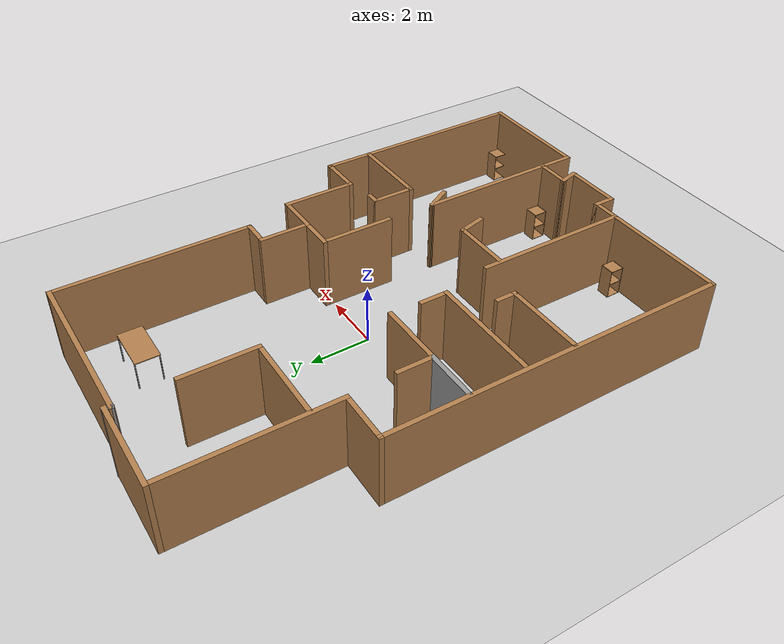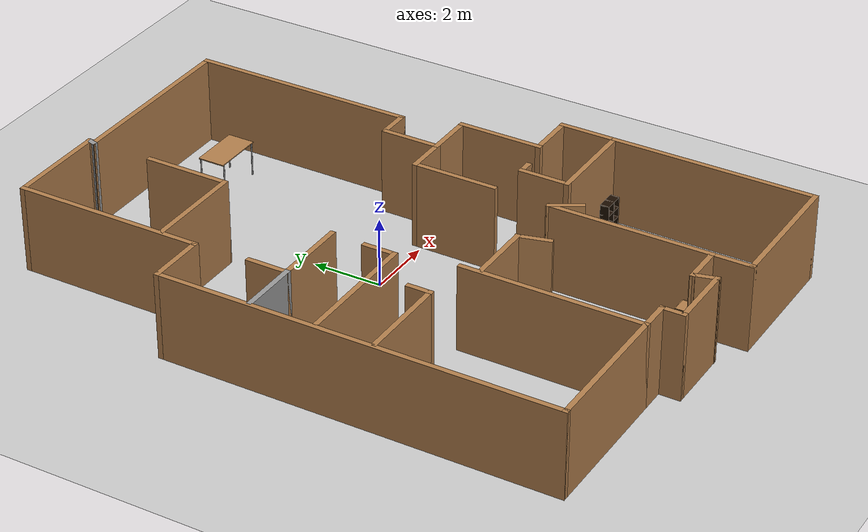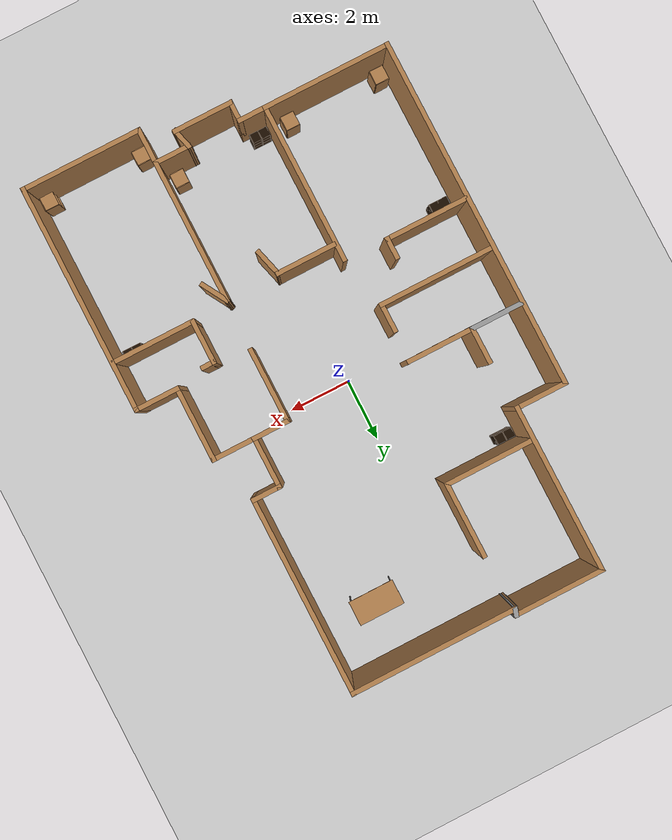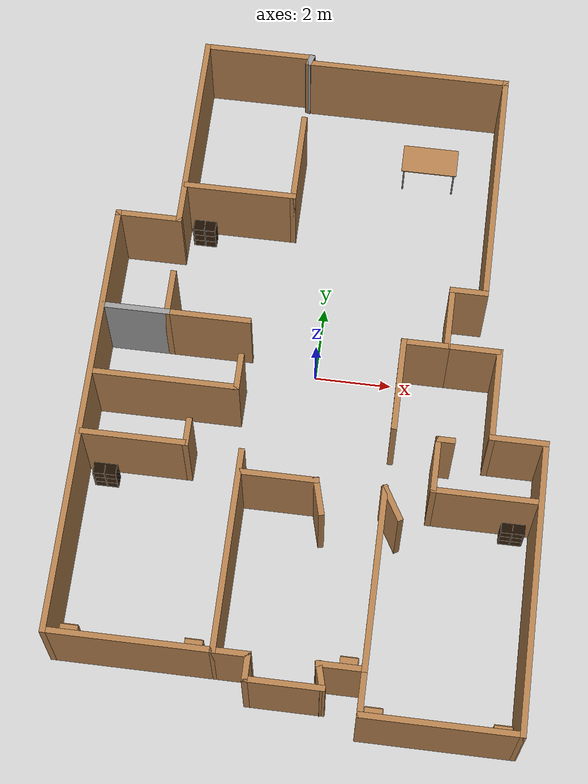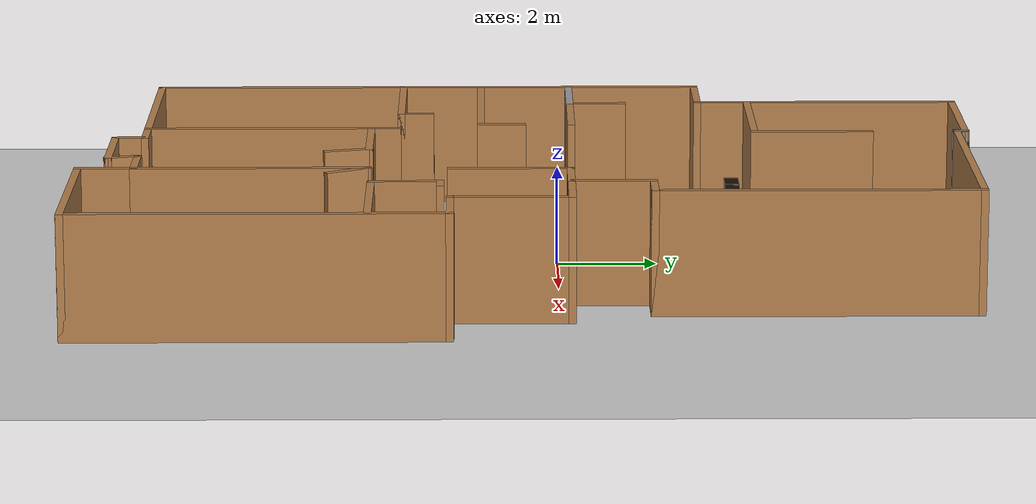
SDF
<sdf version="1.6">
 <world name="default">
  <light name="sun" type="directional">
   <pose>0 0 10 0 -0 0</pose>
   <diffuse>0.8 0.8 0.8 1</diffuse>
   <specular>0.2 0.2 0.2 1</specular>
   <attenuation>
    <range>1000</range>
    <constant>0.9</constant>
    <linear>0.01</linear>
    <quadratic>0.001</quadratic>
   </attenuation>
   <direction>-0.5 0.1 -0.9</direction>
  </light>
  <model name="ground_plane">
   <static>1</static>
   <link name="link">
    <collision name="collision">
     <geometry><plane><normal>0 0 1</normal><size>100 100</size></plane></geometry>
     <surface>
      <contact><collide_bitmask>65535</collide_bitmask></contact>
      <friction><ode><mu>100</mu><mu2>50</mu2></ode></friction>
     </surface>
    </collision>
    <visual name="visual">
     <cast_shadows>0</cast_shadows>
     <geometry><plane><normal>0 0 1</normal><size>100 100</size></plane></geometry>
     <material>
      <script><uri>file://media/materials/scripts/gazebo.material</uri><name>Gazebo/Grey</name></script>
     </material>
    </visual>
   </link>
  </model>
  <gravity>0 0 -9.8</gravity>
  <magnetic_field>6e-06 2.3e-05 -4.2e-05</magnetic_field>
  <atmosphere type="adiabatic"/>
  <physics name="default_physics" default="0" type="ode">
   <max_step_size>0.001</max_step_size>
   <real_time_factor>1</real_time_factor>
   <real_time_update_rate>1000</real_time_update_rate>
  </physics>
  <scene><ambient>0.4 0.4 0.4 1</ambient><background>0.7 0.7 0.7 1</background><shadows>1</shadows></scene>
  <audio><device>default</device></audio>
  <spherical_coordinates>
   <surface_model>EARTH_WGS84</surface_model>
   <latitude_deg>0</latitude_deg>
   <longitude_deg>0</longitude_deg>
   <elevation>0</elevation>
   <heading_deg>0</heading_deg>
  </spherical_coordinates>
  <model name="map_60">
   <pose>0.211771 -0.553556 0 0 -0 0</pose>
   <link name="Wall_0">
    <collision name="Wall_0_Collision">
     <geometry><box><size>3 0.15 2.5</size></box></geometry>
     <pose>0 0 1.25 0 -0 0</pose>
    </collision>
    <visual name="Wall_0_Visual">
     <pose>0 0 1.25 0 -0 0</pose>
     <geometry><box><size>3 0.15 2.5</size></box></geometry>
     <material>
      <script><uri>file://media/materials/scripts/gazebo.material</uri><name>Gazebo/Wood</name></script>
      <ambient>1 1 1 1</ambient>
     </material>
     <meta><layer>0</layer></meta>
    </visual>
    <pose>-2.77235 8.90048 0 0 -0 3.14159</pose>
   </link>
   <link name="Wall_1">
    <collision name="Wall_1_Collision">
     <geometry><box><size>5.5 0.15 2.5</size></box></geometry>
     <pose>0 0 1.25 0 -0 0</pose>
    </collision>
    <visual name="Wall_1_Visual">
     <pose>0 0 1.25 0 -0 0</pose>
     <geometry><box><size>5.5 0.15 2.5</size></box></geometry>
     <material>
      <script><uri>file://media/materials/scripts/gazebo.material</uri><name>Gazebo/Wood</name></script>
      <ambient>1 1 1 1</ambient>
     </material>
     <meta><layer>0</layer></meta>
    </visual>
    <pose>-4.19735 6.22548 0 0 -0 -1.5708</pose>
   </link>
   <link name="Wall_10">
    <collision name="Wall_10_Collision">
     <geometry><box><size>5.25 0.15 2.5</size></box></geometry>
     <pose>0 0 1.25 0 -0 0</pose>
    </collision>
    <visual name="Wall_10_Visual">
     <pose>0 0 1.25 0 -0 0</pose>
     <geometry><box><size>5.25 0.15 2.5</size></box></geometry>
     <material>
      <script><uri>file://media/materials/scripts/gazebo.material</uri><name>Gazebo/Wood</name></script>
      <ambient>1 1 1 1</ambient>
     </material>
     <meta><layer>0</layer></meta>
    </visual>
    <pose>-1.69735 -5.24952 0 0 -0 1.5708</pose>
   </link>
   <link name="Wall_12">
    <collision name="Wall_12_Collision">
     <geometry><box><size>1 0.15 2.5</size></box></geometry>
     <pose>0 0 1.25 0 -0 0</pose>
    </collision>
    <visual name="Wall_12_Visual">
     <pose>0 0 1.25 0 -0 0</pose>
     <geometry><box><size>1 0.15 2.5</size></box></geometry>
     <material>
      <script><uri>file://media/materials/scripts/gazebo.material</uri><name>Gazebo/Wood</name></script>
      <ambient>1 1 1 1</ambient>
     </material>
     <meta><layer>0</layer></meta>
    </visual>
    <pose>-1.27235 -7.79952 0 0 -0 0</pose>
   </link>
   <link name="Wall_13">
    <collision name="Wall_13_Collision">
     <geometry><box><size>0.75 0.15 2.5</size></box></geometry>
     <pose>0 0 1.25 0 -0 0</pose>
    </collision>
    <visual name="Wall_13_Visual">
     <pose>0 0 1.25 0 -0 0</pose>
     <geometry><box><size>0.75 0.15 2.5</size></box></geometry>
     <material>
      <script><uri>file://media/materials/scripts/gazebo.material</uri><name>Gazebo/Wood</name></script>
      <ambient>1 1 1 1</ambient>
     </material>
     <meta><layer>0</layer></meta>
    </visual>
    <pose>-0.847354 -8.09952 0 0 -0 -1.5708</pose>
   </link>
   <link name="Wall_14">
    <collision name="Wall_14_Collision">
     <geometry><box><size>2 0.15 2.5</size></box></geometry>
     <pose>0 0 1.25 0 -0 0</pose>
    </collision>
    <visual name="Wall_14_Visual">
     <pose>0 0 1.25 0 -0 0</pose>
     <geometry><box><size>2 0.15 2.5</size></box></geometry>
     <material>
      <script><uri>file://media/materials/scripts/gazebo.material</uri><name>Gazebo/Wood</name></script>
      <ambient>1 1 1 1</ambient>
     </material>
     <meta><layer>0</layer></meta>
    </visual>
    <pose>0.077646 -8.39952 0 0 -0 0</pose>
   </link>
   <link name="Wall_15">
    <collision name="Wall_15_Collision">
     <geometry><box><size>0.75 0.15 2.5</size></box></geometry>
     <pose>0 0 1.25 0 -0 0</pose>
    </collision>
    <visual name="Wall_15_Visual">
     <pose>0 0 1.25 0 -0 0</pose>
     <geometry><box><size>0.75 0.15 2.5</size></box></geometry>
     <material>
      <script><uri>file://media/materials/scripts/gazebo.material</uri><name>Gazebo/Wood</name></script>
      <ambient>1 1 1 1</ambient>
     </material>
     <meta><layer>0</layer></meta>
    </visual>
    <pose>0.925 -8.10974 0 0 -0 1.8326</pose>
   </link>
   <link name="Wall_16">
    <collision name="Wall_16_Collision">
     <geometry><box><size>1.25 0.15 2.5</size></box></geometry>
     <pose>0 0 1.25 0 -0 0</pose>
    </collision>
    <visual name="Wall_16_Visual">
     <pose>0 0 1.25 0 -0 0</pose>
     <geometry><box><size>1.25 0.15 2.5</size></box></geometry>
     <material>
      <script><uri>file://media/materials/scripts/gazebo.material</uri><name>Gazebo/Wood</name></script>
      <ambient>1 1 1 1</ambient>
     </material>
     <meta><layer>0</layer></meta>
    </visual>
    <pose>1.39735 -7.81996 0 0 -0 0</pose>
   </link>
   <link name="Wall_17">
    <collision name="Wall_17_Collision">
     <geometry><box><size>1.25 0.15 2.5</size></box></geometry>
     <pose>0 0 1.25 0 -0 0</pose>
    </collision>
    <visual name="Wall_17_Visual">
     <pose>0 0 1.25 0 -0 0</pose>
     <geometry><box><size>1.25 0.15 2.5</size></box></geometry>
     <material>
      <script><uri>file://media/materials/scripts/gazebo.material</uri><name>Gazebo/Wood</name></script>
      <ambient>1 1 1 1</ambient>
     </material>
     <meta><layer>0</layer></meta>
    </visual>
    <pose>1.94735 -8.36996 0 0 -0 -1.5708</pose>
   </link>
   <link name="Wall_18">
    <collision name="Wall_18_Collision">
     <geometry><box><size>4 0.15 2.5</size></box></geometry>
     <pose>0 0 1.25 0 -0 0</pose>
    </collision>
    <visual name="Wall_18_Visual">
     <pose>0 0 1.25 0 -0 0</pose>
     <geometry><box><size>4 0.15 2.5</size></box></geometry>
     <material>
      <script><uri>file://media/materials/scripts/gazebo.material</uri><name>Gazebo/Wood</name></script>
      <ambient>1 1 1 1</ambient>
     </material>
     <meta><layer>0</layer></meta>
    </visual>
    <pose>3.87236 -8.91996 0 0 -0 0</pose>
   </link>
   <link name="Wall_19">
    <collision name="Wall_19_Collision">
     <geometry><box><size>7.5 0.15 2.5</size></box></geometry>
     <pose>0 0 1.25 0 -0 0</pose>
    </collision>
    <visual name="Wall_19_Visual">
     <pose>0 0 1.25 0 -0 0</pose>
     <geometry><box><size>7.5 0.15 2.5</size></box></geometry>
     <material>
      <script><uri>file://media/materials/scripts/gazebo.material</uri><name>Gazebo/Wood</name></script>
      <ambient>1 1 1 1</ambient>
     </material>
     <meta><layer>0</layer></meta>
    </visual>
    <pose>5.79735 -5.24496 0 0 -0 1.5708</pose>
   </link>
   <link name="Wall_2">
    <collision name="Wall_2_Collision">
     <geometry><box><size>1.75 0.15 2.5</size></box></geometry>
     <pose>0 0 1.25 0 -0 0</pose>
    </collision>
    <visual name="Wall_2_Visual">
     <pose>0 0 1.25 0 -0 0</pose>
     <geometry><box><size>1.75 0.15 2.5</size></box></geometry>
     <material>
      <script><uri>file://media/materials/scripts/gazebo.material</uri><name>Gazebo/Wood</name></script>
      <ambient>1 1 1 1</ambient>
     </material>
     <meta><layer>0</layer></meta>
    </visual>
    <pose>-4.99735 3.55048 0 0 -0 3.14159</pose>
   </link>
   <link name="Wall_20">
    <collision name="Wall_20_Collision">
     <geometry><box><size>1.5 0.15 2.5</size></box></geometry>
     <pose>0 0 1.25 0 -0 0</pose>
    </collision>
    <visual name="Wall_20_Visual">
     <pose>0 0 1.25 0 -0 0</pose>
     <geometry><box><size>1.5 0.15 2.5</size></box></geometry>
     <material>
      <script><uri>file://media/materials/scripts/gazebo.material</uri><name>Gazebo/Wood</name></script>
      <ambient>1 1 1 1</ambient>
     </material>
     <meta><layer>0</layer></meta>
    </visual>
    <pose>5.12235 -1.56996 0 0 -0 3.14159</pose>
   </link>
   <link name="Wall_21">
    <collision name="Wall_21_Collision">
     <geometry><box><size>2.5 0.15 2.5</size></box></geometry>
     <pose>0 0 1.25 0 -0 0</pose>
    </collision>
    <visual name="Wall_21_Visual">
     <pose>0 0 1.25 0 -0 0</pose>
     <geometry><box><size>2.5 0.15 2.5</size></box></geometry>
     <material>
      <script><uri>file://media/materials/scripts/gazebo.material</uri><name>Gazebo/Wood</name></script>
      <ambient>1 1 1 1</ambient>
     </material>
     <meta><layer>0</layer></meta>
    </visual>
    <pose>4.44735 -0.394963 0 0 -0 1.5708</pose>
   </link>
   <link name="Wall_22">
    <collision name="Wall_22_Collision">
     <geometry><box><size>1.5 0.15 2.5</size></box></geometry>
     <pose>0 0 1.25 0 -0 0</pose>
    </collision>
    <visual name="Wall_22_Visual">
     <pose>0 0 1.25 0 -0 0</pose>
     <geometry><box><size>1.5 0.15 2.5</size></box></geometry>
     <material>
      <script><uri>file://media/materials/scripts/gazebo.material</uri><name>Gazebo/Wood</name></script>
      <ambient>1 1 1 1</ambient>
     </material>
     <meta><layer>0</layer></meta>
    </visual>
    <pose>3.77236 0.780037 0 0 -0 3.14159</pose>
   </link>
   <link name="Wall_23">
    <collision name="Wall_23_Collision">
     <geometry><box><size>1.75 0.15 2.5</size></box></geometry>
     <pose>0 0 1.25 0 -0 0</pose>
    </collision>
    <visual name="Wall_23_Visual">
     <pose>0 0 1.25 0 -0 0</pose>
     <geometry><box><size>1.75 0.15 2.5</size></box></geometry>
     <material>
      <script><uri>file://media/materials/scripts/gazebo.material</uri><name>Gazebo/Wood</name></script>
      <ambient>1 1 1 1</ambient>
     </material>
     <meta><layer>0</layer></meta>
    </visual>
    <pose>3.09735 1.58004 0 0 -0 1.5708</pose>
   </link>
   <link name="Wall_24">
    <collision name="Wall_24_Collision">
     <geometry><box><size>1 0.15 2.5</size></box></geometry>
     <pose>0 0 1.25 0 -0 0</pose>
    </collision>
    <visual name="Wall_24_Visual">
     <pose>0 0 1.25 0 -0 0</pose>
     <geometry><box><size>1 0.15 2.5</size></box></geometry>
     <material>
      <script><uri>file://media/materials/scripts/gazebo.material</uri><name>Gazebo/Wood</name></script>
      <ambient>1 1 1 1</ambient>
     </material>
     <meta><layer>0</layer></meta>
    </visual>
    <pose>3.52236 2.38004 0 0 -0 0</pose>
   </link>
   <link name="Wall_25">
    <collision name="Wall_25_Collision">
     <geometry><box><size>6.5 0.15 2.5</size></box></geometry>
     <pose>0 0 1.25 0 -0 0</pose>
    </collision>
    <visual name="Wall_25_Visual">
     <pose>0 0 1.25 0 -0 0</pose>
     <geometry><box><size>6.5 0.15 2.5</size></box></geometry>
     <material>
      <script><uri>file://media/materials/scripts/gazebo.material</uri><name>Gazebo/Wood</name></script>
      <ambient>1 1 1 1</ambient>
     </material>
     <meta><layer>0</layer></meta>
    </visual>
    <pose>3.94735 5.55504 0 0 -0 1.5708</pose>
   </link>
   <link name="Wall_26">
    <collision name="Wall_26_Collision">
     <geometry><box><size>5.5 0.15 2.5</size></box></geometry>
     <pose>0 0 1.25 0 -0 0</pose>
    </collision>
    <visual name="Wall_26_Visual">
     <pose>0 0 1.25 0 -0 0</pose>
     <geometry><box><size>5.5 0.15 2.5</size></box></geometry>
     <material>
      <script><uri>file://media/materials/scripts/gazebo.material</uri><name>Gazebo/Wood</name></script>
      <ambient>1 1 1 1</ambient>
     </material>
     <meta><layer>0</layer></meta>
    </visual>
    <pose>1.27235 8.73004 0 0 -0 3.14159</pose>
   </link>
   <link name="Wall_28">
    <collision name="Wall_28_Collision">
     <geometry><box><size>0.329188 0.15 2.5</size></box></geometry>
     <pose>0 0 1.25 0 -0 0</pose>
    </collision>
    <visual name="Wall_28_Visual">
     <pose>0 0 1.25 0 -0 0</pose>
     <geometry><box><size>0.329188 0.15 2.5</size></box></geometry>
     <material>
      <script><uri>file://media/materials/scripts/gazebo.material</uri><name>Gazebo/Grey</name></script>
      <ambient>1 1 1 1</ambient>
     </material>
     <meta><layer>0</layer></meta>
    </visual>
    <pose>-1.375 8.81526 0 0 -0 1.25711</pose>
   </link>
   <link name="Wall_30">
    <collision name="Wall_30_Collision">
     <geometry><box><size>1.75 0.15 2.5</size></box></geometry>
     <pose>0 0 1.25 0 -0 0</pose>
    </collision>
    <visual name="Wall_30_Visual">
     <pose>0 0 1.25 0 -0 0</pose>
     <geometry><box><size>1.75 0.15 2.5</size></box></geometry>
     <material>
      <script><uri>file://media/materials/scripts/gazebo.material</uri><name>Gazebo/Grey</name></script>
      <ambient>1 1 1 1</ambient>
     </material>
     <meta><layer>0</layer></meta>
    </visual>
    <pose>-4.90979 0.867221 0 0 -0 0</pose>
   </link>
   <link name="Wall_31">
    <collision name="Wall_31_Collision">
     <geometry><box><size>1.25 0.15 2.5</size></box></geometry>
     <pose>0 0 1.25 0 -0 0</pose>
    </collision>
    <visual name="Wall_31_Visual">
     <pose>0 0 1.25 0 -0 0</pose>
     <geometry><box><size>1.25 0.15 2.5</size></box></geometry>
     <material>
      <script><uri>file://media/materials/scripts/gazebo.material</uri><name>Gazebo/Wood</name></script>
      <ambient>1 1 1 1</ambient>
     </material>
     <meta><layer>0</layer></meta>
    </visual>
    <pose>-4.10979 1.41722 0 0 -0 1.5708</pose>
   </link>
   <link name="Wall_33">
    <collision name="Wall_33_Collision">
     <geometry><box><size>2.75 0.15 2.5</size></box></geometry>
     <pose>0 0 1.25 0 -0 0</pose>
    </collision>
    <visual name="Wall_33_Visual">
     <pose>0 0 1.25 0 -0 0</pose>
     <geometry><box><size>2.75 0.15 2.5</size></box></geometry>
     <material>
      <script><uri>file://media/materials/scripts/gazebo.material</uri><name>Gazebo/Wood</name></script>
      <ambient>1 1 1 1</ambient>
     </material>
     <meta><layer>0</layer></meta>
    </visual>
    <pose>4.4283 -3.12281 0 0 -0 3.14159</pose>
   </link>
   <link name="Wall_34">
    <collision name="Wall_34_Collision">
     <geometry><box><size>1.5 0.15 2.5</size></box></geometry>
     <pose>0 0 1.25 0 -0 0</pose>
    </collision>
    <visual name="Wall_34_Visual">
     <pose>0 0 1.25 0 -0 0</pose>
     <geometry><box><size>1.5 0.15 2.5</size></box></geometry>
     <material>
      <script><uri>file://media/materials/scripts/gazebo.material</uri><name>Gazebo/Wood</name></script>
      <ambient>1 1 1 1</ambient>
     </material>
     <meta><layer>0</layer></meta>
    </visual>
    <pose>3.1283 -2.44781 0 0 -0 1.5708</pose>
   </link>
   <link name="Wall_38">
    <collision name="Wall_38_Collision">
     <geometry><box><size>4.75 0.15 2.5</size></box></geometry>
     <pose>0 0 1.25 0 -0 0</pose>
    </collision>
    <visual name="Wall_38_Visual">
     <pose>0 0 1.25 0 -0 0</pose>
     <geometry><box><size>4.75 0.15 2.5</size></box></geometry>
     <material>
      <script><uri>file://media/materials/scripts/gazebo.material</uri><name>Gazebo/Wood</name></script>
      <ambient>1 1 1 1</ambient>
     </material>
     <meta><layer>0</layer></meta>
    </visual>
    <pose>1.94735 -5.51996 0 0 -0 1.5708</pose>
   </link>
   <link name="Wall_40">
    <collision name="Wall_40_Collision">
     <geometry><box><size>2 0.15 2.5</size></box></geometry>
     <pose>0 0 1.25 0 -0 0</pose>
    </collision>
    <visual name="Wall_40_Visual">
     <pose>0 0 1.25 0 -0 0</pose>
     <geometry><box><size>2 0.15 2.5</size></box></geometry>
     <material>
      <script><uri>file://media/materials/scripts/gazebo.material</uri><name>Gazebo/Wood</name></script>
      <ambient>1 1 1 1</ambient>
     </material>
     <meta><layer>0</layer></meta>
    </visual>
    <pose>-0.688356 -3.22921 0 0 -0 0</pose>
   </link>
   <link name="Wall_41">
    <collision name="Wall_41_Collision">
     <geometry><box><size>1 0.15 2.5</size></box></geometry>
     <pose>0 0 1.25 0 -0 0</pose>
    </collision>
    <visual name="Wall_41_Visual">
     <pose>0 0 1.25 0 -0 0</pose>
     <geometry><box><size>1 0.15 2.5</size></box></geometry>
     <material>
      <script><uri>file://media/materials/scripts/gazebo.material</uri><name>Gazebo/Wood</name></script>
      <ambient>1 1 1 1</ambient>
     </material>
     <meta><layer>0</layer></meta>
    </visual>
    <pose>0.346642 -3.63973 0 0 -0 -1.309</pose>
   </link>
   <link name="Wall_43">
    <collision name="Wall_43_Collision">
     <geometry><box><size>1 0.15 2.5</size></box></geometry>
     <pose>0 0 1.25 0 -0 0</pose>
    </collision>
    <visual name="Wall_43_Visual">
     <pose>0 0 1.25 0 -0 0</pose>
     <geometry><box><size>1 0.15 2.5</size></box></geometry>
     <material>
      <script><uri>file://media/materials/scripts/gazebo.material</uri><name>Gazebo/Wood</name></script>
      <ambient>1 1 1 1</ambient>
     </material>
     <meta><layer>0</layer></meta>
    </visual>
    <pose>2.15985 -3.58802 0 0 -0 -1.0472</pose>
   </link>
   <link name="Wall_52">
    <collision name="Wall_52_Collision">
     <geometry><box><size>2.75 0.15 2.5</size></box></geometry>
     <pose>0 0 1.25 0 -0 0</pose>
    </collision>
    <visual name="Wall_52_Visual">
     <pose>0 0 1.25 0 -0 0</pose>
     <geometry><box><size>2.75 0.15 2.5</size></box></geometry>
     <material>
      <script><uri>file://media/materials/scripts/gazebo.material</uri><name>Gazebo/Wood</name></script>
      <ambient>1 1 1 1</ambient>
     </material>
     <meta><layer>0</layer></meta>
    </visual>
    <pose>-4.40979 -2.644 0 0 -0 0</pose>
   </link>
   <link name="Wall_53">
    <collision name="Wall_53_Collision">
     <geometry><box><size>0.75 0.15 2.5</size></box></geometry>
     <pose>0 0 1.25 0 -0 0</pose>
    </collision>
    <visual name="Wall_53_Visual">
     <pose>0 0 1.25 0 -0 0</pose>
     <geometry><box><size>0.75 0.15 2.5</size></box></geometry>
     <material>
      <script><uri>file://media/materials/scripts/gazebo.material</uri><name>Gazebo/Wood</name></script>
      <ambient>1 1 1 1</ambient>
     </material>
     <meta><layer>0</layer></meta>
    </visual>
    <pose>-3.10979 -2.34401 0 0 -0 1.5708</pose>
   </link>
   <link name="Wall_55">
    <collision name="Wall_55_Collision">
     <geometry><box><size>3 0.15 2.5</size></box></geometry>
     <pose>0 0 1.25 0 -0 0</pose>
    </collision>
    <visual name="Wall_55_Visual">
     <pose>0 0 1.25 0 -0 0</pose>
     <geometry><box><size>3 0.15 2.5</size></box></geometry>
     <material>
      <script><uri>file://media/materials/scripts/gazebo.material</uri><name>Gazebo/Wood</name></script>
      <ambient>1 1 1 1</ambient>
     </material>
     <meta><layer>0</layer></meta>
    </visual>
    <pose>-2.74198 4.59125 0 0 -0 0</pose>
   </link>
   <link name="Wall_56">
    <collision name="Wall_56_Collision">
     <geometry><box><size>2.5 0.15 2.5</size></box></geometry>
     <pose>0 0 1.25 0 -0 0</pose>
    </collision>
    <visual name="Wall_56_Visual">
     <pose>0 0 1.25 0 -0 0</pose>
     <geometry><box><size>2.5 0.15 2.5</size></box></geometry>
     <material>
      <script><uri>file://media/materials/scripts/gazebo.material</uri><name>Gazebo/Wood</name></script>
      <ambient>1 1 1 1</ambient>
     </material>
     <meta><layer>0</layer></meta>
    </visual>
    <pose>-1.31698 5.76625 0 0 -0 1.5708</pose>
   </link>
   <link name="Wall_58">
    <collision name="Wall_58_Collision">
     <geometry><box><size>1.25 0.15 2.5</size></box></geometry>
     <pose>0 0 1.25 0 -0 0</pose>
    </collision>
    <visual name="Wall_58_Visual">
     <pose>0 0 1.25 0 -0 0</pose>
     <geometry><box><size>1.25 0.15 2.5</size></box></geometry>
     <material>
      <script><uri>file://media/materials/scripts/gazebo.material</uri><name>Gazebo/Wood</name></script>
      <ambient>1 1 1 1</ambient>
     </material>
     <meta><layer>0</layer></meta>
    </visual>
    <pose>2.54735 0.780037 0 0 -0 3.14159</pose>
   </link>
   <link name="Wall_59">
    <collision name="Wall_59_Collision">
     <geometry><box><size>2.5 0.15 2.5</size></box></geometry>
     <pose>0 0 1.25 0 -0 0</pose>
    </collision>
    <visual name="Wall_59_Visual">
     <pose>0 0 1.25 0 -0 0</pose>
     <geometry><box><size>2.5 0.15 2.5</size></box></geometry>
     <material>
      <script><uri>file://media/materials/scripts/gazebo.material</uri><name>Gazebo/Wood</name></script>
      <ambient>1 1 1 1</ambient>
     </material>
     <meta><layer>0</layer></meta>
    </visual>
    <pose>1.99735 -0.394963 0 0 -0 -1.5708</pose>
   </link>
   <link name="Wall_61">
    <collision name="Wall_61_Collision">
     <geometry><box><size>0.5 0.15 2.5</size></box></geometry>
     <pose>0 0 1.25 0 -0 0</pose>
    </collision>
    <visual name="Wall_61_Visual">
     <pose>0 0 1.25 0 -0 0</pose>
     <geometry><box><size>0.5 0.15 2.5</size></box></geometry>
     <material>
      <script><uri>file://media/materials/scripts/gazebo.material</uri><name>Gazebo/Wood</name></script>
      <ambient>1 1 1 1</ambient>
     </material>
     <meta><layer>0</layer></meta>
    </visual>
    <pose>3.3033 -1.77281 0 0 -0 0</pose>
   </link>
   <link name="Wall_63">
    <collision name="Wall_63_Collision">
     <geometry><box><size>2.25 0.15 2.5</size></box></geometry>
     <pose>0 0 1.25 0 -0 0</pose>
    </collision>
    <visual name="Wall_63_Visual">
     <pose>0 0 1.25 0 -0 0</pose>
     <geometry><box><size>2.25 0.15 2.5</size></box></geometry>
     <material>
      <script><uri>file://media/materials/scripts/gazebo.material</uri><name>Gazebo/Wood</name></script>
      <ambient>1 1 1 1</ambient>
     </material>
     <meta><layer>0</layer></meta>
    </visual>
    <pose>-3.05979 0.867221 0 0 -0 0</pose>
   </link>
   <link name="Wall_68">
    <collision name="Wall_68_Collision">
     <geometry><box><size>3.75 0.15 2.5</size></box></geometry>
     <pose>0 0 1.25 0 -0 0</pose>
    </collision>
    <visual name="Wall_68_Visual">
     <pose>0 0 1.25 0 -0 0</pose>
     <geometry><box><size>3.75 0.15 2.5</size></box></geometry>
     <material>
      <script><uri>file://media/materials/scripts/gazebo.material</uri><name>Gazebo/Wood</name></script>
      <ambient>1 1 1 1</ambient>
     </material>
     <meta><layer>0</layer></meta>
    </visual>
    <pose>-3.85659 -0.994793 0 0 -0 0</pose>
   </link>
   <link name="Wall_70">
    <collision name="Wall_70_Collision">
     <geometry><box><size>1 0.15 2.5</size></box></geometry>
     <pose>0 0 1.25 0 -0 0</pose>
    </collision>
    <visual name="Wall_70_Visual">
     <pose>0 0 1.25 0 -0 0</pose>
     <geometry><box><size>1 0.15 2.5</size></box></geometry>
     <material>
      <script><uri>file://media/materials/scripts/gazebo.material</uri><name>Gazebo/Wood</name></script>
      <ambient>1 1 1 1</ambient>
     </material>
     <meta><layer>0</layer></meta>
    </visual>
    <pose>-2.05659 -0.569793 0 0 -0 1.5708</pose>
   </link>
   <link name="Wall_8">
    <collision name="Wall_8_Collision">
     <geometry><box><size>11.5 0.15 2.5</size></box></geometry>
     <pose>0 0 1.25 0 -0 0</pose>
    </collision>
    <visual name="Wall_8_Visual">
     <pose>0 0 1.25 0 -0 0</pose>
     <geometry><box><size>11.5 0.15 2.5</size></box></geometry>
     <material>
      <script><uri>file://media/materials/scripts/gazebo.material</uri><name>Gazebo/Wood</name></script>
      <ambient>1 1 1 1</ambient>
     </material>
     <meta><layer>0</layer></meta>
    </visual>
    <pose>-5.79735 -2.12452 0 0 -0 -1.5708</pose>
   </link>
   <link name="Wall_9">
    <collision name="Wall_9_Collision">
     <geometry><box><size>4.25 0.15 2.5</size></box></geometry>
     <pose>0 0 1.25 0 -0 0</pose>
    </collision>
    <visual name="Wall_9_Visual">
     <pose>0 0 1.25 0 -0 0</pose>
     <geometry><box><size>4.25 0.15 2.5</size></box></geometry>
     <material>
      <script><uri>file://media/materials/scripts/gazebo.material</uri><name>Gazebo/Wood</name></script>
      <ambient>1 1 1 1</ambient>
     </material>
     <meta><layer>0</layer></meta>
    </visual>
    <pose>-3.74735 -7.79952 0 0 -0 0</pose>
   </link>
   <static>1</static>
  </model>
  <model name="cabinet">
   <static>1</static>
   <link name="cabinet_bottom_plate">
    <inertial>
     <pose>0 0 -1 0 -0 0</pose>
     <inertia><ixx>2.05</ixx><ixy>0</ixy><ixz>0</ixz><iyy>2.05</iyy><iyz>0</iyz><izz>2.05</izz></inertia>
     <mass>25</mass>
    </inertial>
    <collision name="cabinet_bottom_plate_geom">
     <pose>0 0 0.01 0 -0 0</pose>
     <geometry><box><size>0.45 0.45 0.02</size></box></geometry>
    </collision>
    <visual name="cabinet_bottom_plate_geom_visual">
     <pose>0 0 0.01 0 -0 0</pose>
     <geometry><box><size>0.45 0.45 0.02</size></box></geometry>
     <material>
      <script><uri>file://media/materials/scripts/gazebo.material</uri><name>Gazebo/Wood</name></script>
     </material>
    </visual>
    <collision name="cabinet_bottom_plate_geom_cabinet_back_plate">
     <pose>0.235 0 0.51 0 -0 0</pose>
     <geometry><box><size>0.02 0.45 1.02</size></box></geometry>
    </collision>
    <visual name="cabinet_bottom_plate_geom_cabinet_back_plate_visual">
     <pose>0.235 0 0.51 0 -0 0</pose>
     <geometry><box><size>0.02 0.45 1.02</size></box></geometry>
     <material>
      <script><uri>file://media/materials/scripts/gazebo.material</uri><name>Gazebo/Wood</name></script>
     </material>
    </visual>
    <collision name="cabinet_bottom_plate_geom_cabinet_left_plate">
     <pose>0 0.235 0.51 0 -0 0</pose>
     <geometry><box><size>0.45 0.02 1.02</size></box></geometry>
    </collision>
    <visual name="cabinet_bottom_plate_geom_cabinet_left_plate_visual">
     <pose>0 0.235 0.51 0 -0 0</pose>
     <geometry><box><size>0.45 0.02 1.02</size></box></geometry>
     <material>
      <script><uri>file://media/materials/scripts/gazebo.material</uri><name>Gazebo/Wood</name></script>
     </material>
    </visual>
    <collision name="cabinet_bottom_plate_geom_cabinet_middle_plate">
     <pose>0 0 0.51 0 -0 0</pose>
     <geometry><box><size>0.45 0.45 0.02</size></box></geometry>
    </collision>
    <visual name="cabinet_bottom_plate_geom_cabinet_middle_plate_visual">
     <pose>0 0 0.51 0 -0 0</pose>
     <geometry><box><size>0.45 0.45 0.02</size></box></geometry>
     <material>
      <script><uri>file://media/materials/scripts/gazebo.material</uri><name>Gazebo/Wood</name></script>
     </material>
    </visual>
    <collision name="cabinet_bottom_plate_geom_cabinet_right_plate">
     <pose>0 -0.235 0.51 0 -0 0</pose>
     <geometry><box><size>0.45 0.02 1.02</size></box></geometry>
    </collision>
    <visual name="cabinet_bottom_plate_geom_cabinet_right_plate_visual">
     <pose>0 -0.235 0.51 0 -0 0</pose>
     <geometry><box><size>0.45 0.02 1.02</size></box></geometry>
     <material>
      <script><uri>file://media/materials/scripts/gazebo.material</uri><name>Gazebo/Wood</name></script>
     </material>
    </visual>
    <collision name="cabinet_bottom_plate_geom_cabinet_top_plate">
     <pose>0 0 1.01 0 -0 0</pose>
     <geometry><box><size>0.45 0.45 0.02</size></box></geometry>
    </collision>
    <visual name="cabinet_bottom_plate_geom_cabinet_top_plate_visual">
     <pose>0 0 1.01 0 -0 0</pose>
     <geometry><box><size>0.45 0.45 0.02</size></box></geometry>
     <material>
      <script><uri>file://media/materials/scripts/gazebo.material</uri><name>Gazebo/Wood</name></script>
     </material>
    </visual>
   </link>
   <pose>-5.20758 -7.98036 0 0 -0 0</pose>
  </model>
  <model name="cabinet_0">
   <static>1</static>
   <link name="cabinet_bottom_plate">
    <inertial>
     <pose>0 0 -1 0 -0 0</pose>
     <inertia><ixx>2.05</ixx><ixy>0</ixy><ixz>0</ixz><iyy>2.05</iyy><iyz>0</iyz><izz>2.05</izz></inertia>
     <mass>25</mass>
    </inertial>
    <collision name="cabinet_bottom_plate_geom">
     <pose>0 0 0.01 0 -0 0</pose>
     <geometry><box><size>0.45 0.45 0.02</size></box></geometry>
    </collision>
    <visual name="cabinet_bottom_plate_geom_visual">
     <pose>0 0 0.01 0 -0 0</pose>
     <geometry><box><size>0.45 0.45 0.02</size></box></geometry>
     <material>
      <script><uri>file://media/materials/scripts/gazebo.material</uri><name>Gazebo/Wood</name></script>
     </material>
    </visual>
    <collision name="cabinet_bottom_plate_geom_cabinet_back_plate">
     <pose>0.235 0 0.51 0 -0 0</pose>
     <geometry><box><size>0.02 0.45 1.02</size></box></geometry>
    </collision>
    <visual name="cabinet_bottom_plate_geom_cabinet_back_plate_visual">
     <pose>0.235 0 0.51 0 -0 0</pose>
     <geometry><box><size>0.02 0.45 1.02</size></box></geometry>
     <material>
      <script><uri>file://media/materials/scripts/gazebo.material</uri><name>Gazebo/Wood</name></script>
     </material>
    </visual>
    <collision name="cabinet_bottom_plate_geom_cabinet_left_plate">
     <pose>0 0.235 0.51 0 -0 0</pose>
     <geometry><box><size>0.45 0.02 1.02</size></box></geometry>
    </collision>
    <visual name="cabinet_bottom_plate_geom_cabinet_left_plate_visual">
     <pose>0 0.235 0.51 0 -0 0</pose>
     <geometry><box><size>0.45 0.02 1.02</size></box></geometry>
     <material>
      <script><uri>file://media/materials/scripts/gazebo.material</uri><name>Gazebo/Wood</name></script>
     </material>
    </visual>
    <collision name="cabinet_bottom_plate_geom_cabinet_middle_plate">
     <pose>0 0 0.51 0 -0 0</pose>
     <geometry><box><size>0.45 0.45 0.02</size></box></geometry>
    </collision>
    <visual name="cabinet_bottom_plate_geom_cabinet_middle_plate_visual">
     <pose>0 0 0.51 0 -0 0</pose>
     <geometry><box><size>0.45 0.45 0.02</size></box></geometry>
     <material>
      <script><uri>file://media/materials/scripts/gazebo.material</uri><name>Gazebo/Wood</name></script>
     </material>
    </visual>
    <collision name="cabinet_bottom_plate_geom_cabinet_right_plate">
     <pose>0 -0.235 0.51 0 -0 0</pose>
     <geometry><box><size>0.45 0.02 1.02</size></box></geometry>
    </collision>
    <visual name="cabinet_bottom_plate_geom_cabinet_right_plate_visual">
     <pose>0 -0.235 0.51 0 -0 0</pose>
     <geometry><box><size>0.45 0.02 1.02</size></box></geometry>
     <material>
      <script><uri>file://media/materials/scripts/gazebo.material</uri><name>Gazebo/Wood</name></script>
     </material>
    </visual>
    <collision name="cabinet_bottom_plate_geom_cabinet_top_plate">
     <pose>0 0 1.01 0 -0 0</pose>
     <geometry><box><size>0.45 0.45 0.02</size></box></geometry>
    </collision>
    <visual name="cabinet_bottom_plate_geom_cabinet_top_plate_visual">
     <pose>0 0 1.01 0 -0 0</pose>
     <geometry><box><size>0.45 0.45 0.02</size></box></geometry>
     <material>
      <script><uri>file://media/materials/scripts/gazebo.material</uri><name>Gazebo/Wood</name></script>
     </material>
    </visual>
   </link>
   <pose>-2.09411 -7.98099 0 0 -0 0</pose>
  </model>
  <model name="cabinet_1">
   <static>1</static>
   <link name="cabinet_bottom_plate">
    <inertial>
     <pose>0 0 -1 0 -0 0</pose>
     <inertia><ixx>2.05</ixx><ixy>0</ixy><ixz>0</ixz><iyy>2.05</iyy><iyz>0</iyz><izz>2.05</izz></inertia>
     <mass>25</mass>
    </inertial>
    <collision name="cabinet_bottom_plate_geom">
     <pose>0 0 0.01 0 -0 0</pose>
     <geometry><box><size>0.45 0.45 0.02</size></box></geometry>
    </collision>
    <visual name="cabinet_bottom_plate_geom_visual">
     <pose>0 0 0.01 0 -0 0</pose>
     <geometry><box><size>0.45 0.45 0.02</size></box></geometry>
     <material>
      <script><uri>file://media/materials/scripts/gazebo.material</uri><name>Gazebo/Wood</name></script>
     </material>
    </visual>
    <collision name="cabinet_bottom_plate_geom_cabinet_back_plate">
     <pose>0.235 0 0.51 0 -0 0</pose>
     <geometry><box><size>0.02 0.45 1.02</size></box></geometry>
    </collision>
    <visual name="cabinet_bottom_plate_geom_cabinet_back_plate_visual">
     <pose>0.235 0 0.51 0 -0 0</pose>
     <geometry><box><size>0.02 0.45 1.02</size></box></geometry>
     <material>
      <script><uri>file://media/materials/scripts/gazebo.material</uri><name>Gazebo/Wood</name></script>
     </material>
    </visual>
    <collision name="cabinet_bottom_plate_geom_cabinet_left_plate">
     <pose>0 0.235 0.51 0 -0 0</pose>
     <geometry><box><size>0.45 0.02 1.02</size></box></geometry>
    </collision>
    <visual name="cabinet_bottom_plate_geom_cabinet_left_plate_visual">
     <pose>0 0.235 0.51 0 -0 0</pose>
     <geometry><box><size>0.45 0.02 1.02</size></box></geometry>
     <material>
      <script><uri>file://media/materials/scripts/gazebo.material</uri><name>Gazebo/Wood</name></script>
     </material>
    </visual>
    <collision name="cabinet_bottom_plate_geom_cabinet_middle_plate">
     <pose>0 0 0.51 0 -0 0</pose>
     <geometry><box><size>0.45 0.45 0.02</size></box></geometry>
    </collision>
    <visual name="cabinet_bottom_plate_geom_cabinet_middle_plate_visual">
     <pose>0 0 0.51 0 -0 0</pose>
     <geometry><box><size>0.45 0.45 0.02</size></box></geometry>
     <material>
      <script><uri>file://media/materials/scripts/gazebo.material</uri><name>Gazebo/Wood</name></script>
     </material>
    </visual>
    <collision name="cabinet_bottom_plate_geom_cabinet_right_plate">
     <pose>0 -0.235 0.51 0 -0 0</pose>
     <geometry><box><size>0.45 0.02 1.02</size></box></geometry>
    </collision>
    <visual name="cabinet_bottom_plate_geom_cabinet_right_plate_visual">
     <pose>0 -0.235 0.51 0 -0 0</pose>
     <geometry><box><size>0.45 0.02 1.02</size></box></geometry>
     <material>
      <script><uri>file://media/materials/scripts/gazebo.material</uri><name>Gazebo/Wood</name></script>
     </material>
    </visual>
    <collision name="cabinet_bottom_plate_geom_cabinet_top_plate">
     <pose>0 0 1.01 0 -0 0</pose>
     <geometry><box><size>0.45 0.45 0.02</size></box></geometry>
    </collision>
    <visual name="cabinet_bottom_plate_geom_cabinet_top_plate_visual">
     <pose>0 0 1.01 0 -0 0</pose>
     <geometry><box><size>0.45 0.45 0.02</size></box></geometry>
     <material>
      <script><uri>file://media/materials/scripts/gazebo.material</uri><name>Gazebo/Wood</name></script>
     </material>
    </visual>
   </link>
   <pose>2.48169 -9.13605 0 0 -0 0</pose>
  </model>
  <model name="cabinet_2">
   <static>1</static>
   <link name="cabinet_bottom_plate">
    <inertial>
     <pose>0 0 -1 0 -0 0</pose>
     <inertia><ixx>2.05</ixx><ixy>0</ixy><ixz>0</ixz><iyy>2.05</iyy><iyz>0</iyz><izz>2.05</izz></inertia>
     <mass>25</mass>
    </inertial>
    <collision name="cabinet_bottom_plate_geom">
     <pose>0 0 0.01 0 -0 0</pose>
     <geometry><box><size>0.45 0.45 0.02</size></box></geometry>
    </collision>
    <visual name="cabinet_bottom_plate_geom_visual">
     <pose>0 0 0.01 0 -0 0</pose>
     <geometry><box><size>0.45 0.45 0.02</size></box></geometry>
     <material>
      <script><uri>file://media/materials/scripts/gazebo.material</uri><name>Gazebo/Wood</name></script>
     </material>
    </visual>
    <collision name="cabinet_bottom_plate_geom_cabinet_back_plate">
     <pose>0.235 0 0.51 0 -0 0</pose>
     <geometry><box><size>0.02 0.45 1.02</size></box></geometry>
    </collision>
    <visual name="cabinet_bottom_plate_geom_cabinet_back_plate_visual">
     <pose>0.235 0 0.51 0 -0 0</pose>
     <geometry><box><size>0.02 0.45 1.02</size></box></geometry>
     <material>
      <script><uri>file://media/materials/scripts/gazebo.material</uri><name>Gazebo/Wood</name></script>
     </material>
    </visual>
    <collision name="cabinet_bottom_plate_geom_cabinet_left_plate">
     <pose>0 0.235 0.51 0 -0 0</pose>
     <geometry><box><size>0.45 0.02 1.02</size></box></geometry>
    </collision>
    <visual name="cabinet_bottom_plate_geom_cabinet_left_plate_visual">
     <pose>0 0.235 0.51 0 -0 0</pose>
     <geometry><box><size>0.45 0.02 1.02</size></box></geometry>
     <material>
      <script><uri>file://media/materials/scripts/gazebo.material</uri><name>Gazebo/Wood</name></script>
     </material>
    </visual>
    <collision name="cabinet_bottom_plate_geom_cabinet_middle_plate">
     <pose>0 0 0.51 0 -0 0</pose>
     <geometry><box><size>0.45 0.45 0.02</size></box></geometry>
    </collision>
    <visual name="cabinet_bottom_plate_geom_cabinet_middle_plate_visual">
     <pose>0 0 0.51 0 -0 0</pose>
     <geometry><box><size>0.45 0.45 0.02</size></box></geometry>
     <material>
      <script><uri>file://media/materials/scripts/gazebo.material</uri><name>Gazebo/Wood</name></script>
     </material>
    </visual>
    <collision name="cabinet_bottom_plate_geom_cabinet_right_plate">
     <pose>0 -0.235 0.51 0 -0 0</pose>
     <geometry><box><size>0.45 0.02 1.02</size></box></geometry>
    </collision>
    <visual name="cabinet_bottom_plate_geom_cabinet_right_plate_visual">
     <pose>0 -0.235 0.51 0 -0 0</pose>
     <geometry><box><size>0.45 0.02 1.02</size></box></geometry>
     <material>
      <script><uri>file://media/materials/scripts/gazebo.material</uri><name>Gazebo/Wood</name></script>
     </material>
    </visual>
    <collision name="cabinet_bottom_plate_geom_cabinet_top_plate">
     <pose>0 0 1.01 0 -0 0</pose>
     <geometry><box><size>0.45 0.45 0.02</size></box></geometry>
    </collision>
    <visual name="cabinet_bottom_plate_geom_cabinet_top_plate_visual">
     <pose>0 0 1.01 0 -0 0</pose>
     <geometry><box><size>0.45 0.45 0.02</size></box></geometry>
     <material>
      <script><uri>file://media/materials/scripts/gazebo.material</uri><name>Gazebo/Wood</name></script>
     </material>
    </visual>
   </link>
   <pose>5.65055 -9.1933 0 0 -0 0</pose>
  </model>
  <model name="6_Cube_StorageE">
   <link name="Wall_0">
    <pose>0 0 0.01 0 -0 0</pose>
    <inertial>
     <mass>1.6201</mass>
     <inertia><ixx>0.0119</ixx><iyy>0.0631</iyy><izz>0.0513</izz><ixy>0</ixy><ixz>0</ixz><iyz>0</iyz></inertia>
    </inertial>
    <collision name="Wall_0_Collision"><geometry><box><size>0.616 0.296 0.02</size></box></geometry></collision>
    <visual name="Wall_0_Visual">
     <geometry><box><size>0.616 0.296 0.02</size></box></geometry>
     <material>
      <script><uri>file://media/materials/scripts/gazebo.material</uri><name>Gazebo/Grey</name></script>
      <ambient>0.105882 0.0509804 0 1</ambient>
     </material>
    </visual>
   </link>
   <joint name="0_2" type="fixed">
    <pose>-0.308 0 0 0 -0 0</pose>
    <parent>Wall_2</parent>
    <child>Wall_0</child>
    <axis>
     <xyz>1 0 0</xyz>
     <use_parent_model_frame>0</use_parent_model_frame>
     <limit><lower>-1e+16</lower><upper>1e+16</upper></limit>
    </axis>
   </joint>
   <joint name="0_12" type="fixed">
    <parent>Wall_12</parent>
    <child>Wall_0</child>
    <axis>
     <xyz>0 0 1</xyz>
     <use_parent_model_frame>0</use_parent_model_frame>
     <limit><lower>-1e+16</lower><upper>1e+16</upper></limit>
    </axis>
   </joint>
   <joint name="0_4" type="fixed">
    <pose>0.308 0 0 0 -0 0</pose>
    <parent>Wall_4</parent>
    <child>Wall_0</child>
    <axis>
     <xyz>1 0 0</xyz>
     <use_parent_model_frame>0</use_parent_model_frame>
     <limit><lower>-1e+16</lower><upper>1e+16</upper></limit>
    </axis>
   </joint>
   <link name="Wall_10">
    <pose>0 0 0.61 0 -0 0</pose>
    <inertial>
     <mass>1.6201</mass>
     <inertia><ixx>0.0119</ixx><iyy>0.0631</iyy><izz>0.0513</izz><ixy>0</ixy><ixz>0</ixz><iyz>0</iyz></inertia>
    </inertial>
    <collision name="Wall_10_Collision"><geometry><box><size>0.616 0.296 0.02</size></box></geometry></collision>
    <visual name="Wall_10_Visual">
     <geometry><box><size>0.616 0.296 0.02</size></box></geometry>
     <material>
      <script><uri>file://media/materials/scripts/gazebo.material</uri><name>Gazebo/Grey</name></script>
      <ambient>0.105882 0.0509804 0 1</ambient>
     </material>
    </visual>
   </link>
   <joint name="10_2" type="fixed">
    <pose>-0.308 0 0 0 -0 0</pose>
    <parent>Wall_2</parent>
    <child>Wall_10</child>
    <axis>
     <xyz>1 0 0</xyz>
     <use_parent_model_frame>0</use_parent_model_frame>
     <limit><lower>-1e+16</lower><upper>1e+16</upper></limit>
    </axis>
   </joint>
   <joint name="10_12" type="fixed">
    <parent>Wall_12</parent>
    <child>Wall_10</child>
    <axis>
     <xyz>0 0 1</xyz>
     <use_parent_model_frame>0</use_parent_model_frame>
     <limit><lower>-1e+16</lower><upper>1e+16</upper></limit>
    </axis>
   </joint>
   <joint name="10_4" type="fixed">
    <pose>0.308 0 0 0 -0 0</pose>
    <parent>Wall_4</parent>
    <child>Wall_10</child>
    <axis>
     <xyz>1 0 0</xyz>
     <use_parent_model_frame>0</use_parent_model_frame>
     <limit><lower>-1e+16</lower><upper>1e+16</upper></limit>
    </axis>
   </joint>
   <link name="Wall_12">
    <pose>0 0 0.4575 0 -0 0</pose>
    <inertial>
     <mass>2.4065</mass>
     <inertia><ixx>0.0177</ixx><iyy>0.1855</iyy><izz>0.168</izz><ixy>0</ixy><ixz>0</ixz><iyz>0</iyz></inertia>
    </inertial>
    <collision name="Wall_12_Collision"><geometry><box><size>0.02 0.296 0.915</size></box></geometry></collision>
    <visual name="Wall_12_Visual">
     <geometry><box><size>0.02 0.296 0.915</size></box></geometry>
     <material>
      <script><uri>file://media/materials/scripts/gazebo.material</uri><name>Gazebo/Grey</name></script>
      <ambient>0.105882 0.0509804 0 1</ambient>
     </material>
    </visual>
   </link>
   <link name="Wall_2">
    <pose>-0.298 0 0.4575 0 -0 0</pose>
    <inertial>
     <mass>2.4065</mass>
     <inertia><ixx>0.0177</ixx><iyy>0.1855</iyy><izz>0.168</izz><ixy>0</ixy><ixz>0</ixz><iyz>0</iyz></inertia>
    </inertial>
    <collision name="Wall_2_Collision"><geometry><box><size>0.02 0.296 0.915</size></box></geometry></collision>
    <visual name="Wall_2_Visual">
     <geometry><box><size>0.02 0.296 0.915</size></box></geometry>
     <material>
      <script><uri>file://media/materials/scripts/gazebo.material</uri><name>Gazebo/Grey</name></script>
      <ambient>0.105882 0.0509804 0 1</ambient>
     </material>
    </visual>
   </link>
   <link name="Wall_4">
    <pose>0.298 0 0.4575 0 -0 0</pose>
    <inertial>
     <mass>2.4065</mass>
     <inertia><ixx>0.0177</ixx><iyy>0.1855</iyy><izz>0.168</izz><ixy>0</ixy><ixz>0</ixz><iyz>0</iyz></inertia>
    </inertial>
    <collision name="Wall_4_Collision"><geometry><box><size>0.02 0.296 0.915</size></box></geometry></collision>
    <visual name="Wall_4_Visual">
     <geometry><box><size>0.02 0.296 0.915</size></box></geometry>
     <material>
      <script><uri>file://media/materials/scripts/gazebo.material</uri><name>Gazebo/Grey</name></script>
      <ambient>0.105882 0.0509804 0 1</ambient>
     </material>
    </visual>
   </link>
   <link name="Wall_6">
    <pose>0 0 0.905 0 -0 0</pose>
    <inertial>
     <mass>1.6201</mass>
     <inertia><ixx>0.0119</ixx><iyy>0.0631</iyy><izz>0.0513</izz><ixy>0</ixy><ixz>0</ixz><iyz>0</iyz></inertia>
    </inertial>
    <collision name="Wall_6_Collision"><geometry><box><size>0.616 0.296 0.02</size></box></geometry></collision>
    <visual name="Wall_6_Visual">
     <geometry><box><size>0.616 0.296 0.02</size></box></geometry>
     <material>
      <script><uri>file://media/materials/scripts/gazebo.material</uri><name>Gazebo/Grey</name></script>
      <ambient>0.105882 0.0509804 0 1</ambient>
     </material>
    </visual>
   </link>
   <joint name="6_2" type="fixed">
    <pose>-0.308 0 0 0 -0 0</pose>
    <parent>Wall_2</parent>
    <child>Wall_6</child>
    <axis>
     <xyz>2 0 0</xyz>
     <use_parent_model_frame>0</use_parent_model_frame>
     <limit><lower>-1e+16</lower><upper>1e+16</upper></limit>
    </axis>
   </joint>
   <joint name="6_12" type="fixed">
    <parent>Wall_12</parent>
    <child>Wall_6</child>
    <axis>
     <xyz>0 0 1</xyz>
     <use_parent_model_frame>0</use_parent_model_frame>
     <limit><lower>-1e+16</lower><upper>1e+16</upper></limit>
    </axis>
   </joint>
   <joint name="6_4" type="fixed">
    <pose>0.308 0 0 0 -0 0</pose>
    <parent>Wall_4</parent>
    <child>Wall_6</child>
    <axis>
     <xyz>1 0 0</xyz>
     <use_parent_model_frame>0</use_parent_model_frame>
     <limit><lower>-1e+16</lower><upper>1e+16</upper></limit>
    </axis>
   </joint>
   <link name="Wall_8">
    <pose>0 0 0.305 0 -0 0</pose>
    <inertial>
     <mass>1.6201</mass>
     <inertia><ixx>0.0119</ixx><iyy>0.0631</iyy><izz>0.0513</izz><ixy>0</ixy><ixz>0</ixz><iyz>0</iyz></inertia>
    </inertial>
    <collision name="Wall_8_Collision"><geometry><box><size>0.616 0.296 0.02</size></box></geometry></collision>
    <visual name="Wall_8_Visual">
     <geometry><box><size>0.616 0.296 0.02</size></box></geometry>
     <material>
      <script><uri>file://media/materials/scripts/gazebo.material</uri><name>Gazebo/Grey</name></script>
      <ambient>0.105882 0.0509804 0 1</ambient>
     </material>
    </visual>
   </link>
   <joint name="8_2" type="fixed">
    <pose>-0.308 0 0 0 -0 0</pose>
    <parent>Wall_2</parent>
    <child>Wall_8</child>
    <axis>
     <xyz>1 0 0</xyz>
     <use_parent_model_frame>0</use_parent_model_frame>
     <limit><lower>-1e+16</lower><upper>1e+16</upper></limit>
    </axis>
   </joint>
   <joint name="8_12" type="fixed">
    <parent>Wall_12</parent>
    <child>Wall_8</child>
    <axis>
     <xyz>0 0 1</xyz>
     <use_parent_model_frame>0</use_parent_model_frame>
     <limit><lower>-1e+16</lower><upper>1e+16</upper></limit>
    </axis>
   </joint>
   <joint name="8_4" type="fixed">
    <pose>0.308 0 0 0 -0 0</pose>
    <parent>Wall_4</parent>
    <child>Wall_8</child>
    <axis>
     <xyz>1 0 0</xyz>
     <use_parent_model_frame>0</use_parent_model_frame>
     <limit><lower>-1e+16</lower><upper>1e+16</upper></limit>
    </axis>
   </joint>
   <static>1</static>
   <pose>-5.01324 -3.5483 0 0 -0 0</pose>
  </model>
  <model name="6_Cube_StorageE_0">
   <link name="Wall_0">
    <pose>0 0 0.01 0 -0 0</pose>
    <inertial>
     <mass>1.6201</mass>
     <inertia><ixx>0.0119</ixx><iyy>0.0631</iyy><izz>0.0513</izz><ixy>0</ixy><ixz>0</ixz><iyz>0</iyz></inertia>
    </inertial>
    <collision name="Wall_0_Collision"><geometry><box><size>0.616 0.296 0.02</size></box></geometry></collision>
    <visual name="Wall_0_Visual">
     <geometry><box><size>0.616 0.296 0.02</size></box></geometry>
     <material>
      <script><uri>file://media/materials/scripts/gazebo.material</uri><name>Gazebo/Grey</name></script>
      <ambient>0.105882 0.0509804 0 1</ambient>
     </material>
    </visual>
   </link>
   <joint name="0_2" type="fixed">
    <pose>-0.308 0 0 0 -0 0</pose>
    <parent>Wall_2</parent>
    <child>Wall_0</child>
    <axis>
     <xyz>1 0 0</xyz>
     <use_parent_model_frame>0</use_parent_model_frame>
     <limit><lower>-1e+16</lower><upper>1e+16</upper></limit>
    </axis>
   </joint>
   <joint name="0_12" type="fixed">
    <parent>Wall_12</parent>
    <child>Wall_0</child>
    <axis>
     <xyz>0 0 1</xyz>
     <use_parent_model_frame>0</use_parent_model_frame>
     <limit><lower>-1e+16</lower><upper>1e+16</upper></limit>
    </axis>
   </joint>
   <joint name="0_4" type="fixed">
    <pose>0.308 0 0 0 -0 0</pose>
    <parent>Wall_4</parent>
    <child>Wall_0</child>
    <axis>
     <xyz>1 0 0</xyz>
     <use_parent_model_frame>0</use_parent_model_frame>
     <limit><lower>-1e+16</lower><upper>1e+16</upper></limit>
    </axis>
   </joint>
   <link name="Wall_10">
    <pose>0 0 0.61 0 -0 0</pose>
    <inertial>
     <mass>1.6201</mass>
     <inertia><ixx>0.0119</ixx><iyy>0.0631</iyy><izz>0.0513</izz><ixy>0</ixy><ixz>0</ixz><iyz>0</iyz></inertia>
    </inertial>
    <collision name="Wall_10_Collision"><geometry><box><size>0.616 0.296 0.02</size></box></geometry></collision>
    <visual name="Wall_10_Visual">
     <geometry><box><size>0.616 0.296 0.02</size></box></geometry>
     <material>
      <script><uri>file://media/materials/scripts/gazebo.material</uri><name>Gazebo/Grey</name></script>
      <ambient>0.105882 0.0509804 0 1</ambient>
     </material>
    </visual>
   </link>
   <joint name="10_2" type="fixed">
    <pose>-0.308 0 0 0 -0 0</pose>
    <parent>Wall_2</parent>
    <child>Wall_10</child>
    <axis>
     <xyz>1 0 0</xyz>
     <use_parent_model_frame>0</use_parent_model_frame>
     <limit><lower>-1e+16</lower><upper>1e+16</upper></limit>
    </axis>
   </joint>
   <joint name="10_12" type="fixed">
    <parent>Wall_12</parent>
    <child>Wall_10</child>
    <axis>
     <xyz>0 0 1</xyz>
     <use_parent_model_frame>0</use_parent_model_frame>
     <limit><lower>-1e+16</lower><upper>1e+16</upper></limit>
    </axis>
   </joint>
   <joint name="10_4" type="fixed">
    <pose>0.308 0 0 0 -0 0</pose>
    <parent>Wall_4</parent>
    <child>Wall_10</child>
    <axis>
     <xyz>1 0 0</xyz>
     <use_parent_model_frame>0</use_parent_model_frame>
     <limit><lower>-1e+16</lower><upper>1e+16</upper></limit>
    </axis>
   </joint>
   <link name="Wall_12">
    <pose>0 0 0.4575 0 -0 0</pose>
    <inertial>
     <mass>2.4065</mass>
     <inertia><ixx>0.0177</ixx><iyy>0.1855</iyy><izz>0.168</izz><ixy>0</ixy><ixz>0</ixz><iyz>0</iyz></inertia>
    </inertial>
    <collision name="Wall_12_Collision"><geometry><box><size>0.02 0.296 0.915</size></box></geometry></collision>
    <visual name="Wall_12_Visual">
     <geometry><box><size>0.02 0.296 0.915</size></box></geometry>
     <material>
      <script><uri>file://media/materials/scripts/gazebo.material</uri><name>Gazebo/Grey</name></script>
      <ambient>0.105882 0.0509804 0 1</ambient>
     </material>
    </visual>
   </link>
   <link name="Wall_2">
    <pose>-0.298 0 0.4575 0 -0 0</pose>
    <inertial>
     <mass>2.4065</mass>
     <inertia><ixx>0.0177</ixx><iyy>0.1855</iyy><izz>0.168</izz><ixy>0</ixy><ixz>0</ixz><iyz>0</iyz></inertia>
    </inertial>
    <collision name="Wall_2_Collision"><geometry><box><size>0.02 0.296 0.915</size></box></geometry></collision>
    <visual name="Wall_2_Visual">
     <geometry><box><size>0.02 0.296 0.915</size></box></geometry>
     <material>
      <script><uri>file://media/materials/scripts/gazebo.material</uri><name>Gazebo/Grey</name></script>
      <ambient>0.105882 0.0509804 0 1</ambient>
     </material>
    </visual>
   </link>
   <link name="Wall_4">
    <pose>0.298 0 0.4575 0 -0 0</pose>
    <inertial>
     <mass>2.4065</mass>
     <inertia><ixx>0.0177</ixx><iyy>0.1855</iyy><izz>0.168</izz><ixy>0</ixy><ixz>0</ixz><iyz>0</iyz></inertia>
    </inertial>
    <collision name="Wall_4_Collision"><geometry><box><size>0.02 0.296 0.915</size></box></geometry></collision>
    <visual name="Wall_4_Visual">
     <geometry><box><size>0.02 0.296 0.915</size></box></geometry>
     <material>
      <script><uri>file://media/materials/scripts/gazebo.material</uri><name>Gazebo/Grey</name></script>
      <ambient>0.105882 0.0509804 0 1</ambient>
     </material>
    </visual>
   </link>
   <link name="Wall_6">
    <pose>0 0 0.905 0 -0 0</pose>
    <inertial>
     <mass>1.6201</mass>
     <inertia><ixx>0.0119</ixx><iyy>0.0631</iyy><izz>0.0513</izz><ixy>0</ixy><ixz>0</ixz><iyz>0</iyz></inertia>
    </inertial>
    <collision name="Wall_6_Collision"><geometry><box><size>0.616 0.296 0.02</size></box></geometry></collision>
    <visual name="Wall_6_Visual">
     <geometry><box><size>0.616 0.296 0.02</size></box></geometry>
     <material>
      <script><uri>file://media/materials/scripts/gazebo.material</uri><name>Gazebo/Grey</name></script>
      <ambient>0.105882 0.0509804 0 1</ambient>
     </material>
    </visual>
   </link>
   <joint name="6_2" type="fixed">
    <pose>-0.308 0 0 0 -0 0</pose>
    <parent>Wall_2</parent>
    <child>Wall_6</child>
    <axis>
     <xyz>2 0 0</xyz>
     <use_parent_model_frame>0</use_parent_model_frame>
     <limit><lower>-1e+16</lower><upper>1e+16</upper></limit>
    </axis>
   </joint>
   <joint name="6_12" type="fixed">
    <parent>Wall_12</parent>
    <child>Wall_6</child>
    <axis>
     <xyz>0 0 1</xyz>
     <use_parent_model_frame>0</use_parent_model_frame>
     <limit><lower>-1e+16</lower><upper>1e+16</upper></limit>
    </axis>
   </joint>
   <joint name="6_4" type="fixed">
    <pose>0.308 0 0 0 -0 0</pose>
    <parent>Wall_4</parent>
    <child>Wall_6</child>
    <axis>
     <xyz>1 0 0</xyz>
     <use_parent_model_frame>0</use_parent_model_frame>
     <limit><lower>-1e+16</lower><upper>1e+16</upper></limit>
    </axis>
   </joint>
   <link name="Wall_8">
    <pose>0 0 0.305 0 -0 0</pose>
    <inertial>
     <mass>1.6201</mass>
     <inertia><ixx>0.0119</ixx><iyy>0.0631</iyy><izz>0.0513</izz><ixy>0</ixy><ixz>0</ixz><iyz>0</iyz></inertia>
    </inertial>
    <collision name="Wall_8_Collision"><geometry><box><size>0.616 0.296 0.02</size></box></geometry></collision>
    <visual name="Wall_8_Visual">
     <geometry><box><size>0.616 0.296 0.02</size></box></geometry>
     <material>
      <script><uri>file://media/materials/scripts/gazebo.material</uri><name>Gazebo/Grey</name></script>
      <ambient>0.105882 0.0509804 0 1</ambient>
     </material>
    </visual>
   </link>
   <joint name="8_2" type="fixed">
    <pose>-0.308 0 0 0 -0 0</pose>
    <parent>Wall_2</parent>
    <child>Wall_8</child>
    <axis>
     <xyz>1 0 0</xyz>
     <use_parent_model_frame>0</use_parent_model_frame>
     <limit><lower>-1e+16</lower><upper>1e+16</upper></limit>
    </axis>
   </joint>
   <joint name="8_12" type="fixed">
    <parent>Wall_12</parent>
    <child>Wall_8</child>
    <axis>
     <xyz>0 0 1</xyz>
     <use_parent_model_frame>0</use_parent_model_frame>
     <limit><lower>-1e+16</lower><upper>1e+16</upper></limit>
    </axis>
   </joint>
   <joint name="8_4" type="fixed">
    <pose>0.308 0 0 0 -0 0</pose>
    <parent>Wall_4</parent>
    <child>Wall_8</child>
    <axis>
     <xyz>1 0 0</xyz>
     <use_parent_model_frame>0</use_parent_model_frame>
     <limit><lower>-1e+16</lower><upper>1e+16</upper></limit>
    </axis>
   </joint>
   <static>1</static>
   <pose>5.47729 -3.86895 0 0 -0 0</pose>
  </model>
  <model name="cabinet_3">
   <static>1</static>
   <link name="cabinet_bottom_plate">
    <inertial>
     <pose>0 0 -1 0 -0 0</pose>
     <inertia><ixx>2.05</ixx><ixy>0</ixy><ixz>0</ixz><iyy>2.05</iyy><iyz>0</iyz><izz>2.05</izz></inertia>
     <mass>25</mass>
    </inertial>
    <collision name="cabinet_bottom_plate_geom">
     <pose>0 0 0.01 0 -0 0</pose>
     <geometry><box><size>0.45 0.45 0.02</size></box></geometry>
    </collision>
    <visual name="cabinet_bottom_plate_geom_visual">
     <pose>0 0 0.01 0 -0 0</pose>
     <geometry><box><size>0.45 0.45 0.02</size></box></geometry>
     <material>
      <script><uri>file://media/materials/scripts/gazebo.material</uri><name>Gazebo/Wood</name></script>
     </material>
    </visual>
    <collision name="cabinet_bottom_plate_geom_cabinet_back_plate">
     <pose>0.235 0 0.51 0 -0 0</pose>
     <geometry><box><size>0.02 0.45 1.02</size></box></geometry>
    </collision>
    <visual name="cabinet_bottom_plate_geom_cabinet_back_plate_visual">
     <pose>0.235 0 0.51 0 -0 0</pose>
     <geometry><box><size>0.02 0.45 1.02</size></box></geometry>
     <material>
      <script><uri>file://media/materials/scripts/gazebo.material</uri><name>Gazebo/Wood</name></script>
     </material>
    </visual>
    <collision name="cabinet_bottom_plate_geom_cabinet_left_plate">
     <pose>0 0.235 0.51 0 -0 0</pose>
     <geometry><box><size>0.45 0.02 1.02</size></box></geometry>
    </collision>
    <visual name="cabinet_bottom_plate_geom_cabinet_left_plate_visual">
     <pose>0 0.235 0.51 0 -0 0</pose>
     <geometry><box><size>0.45 0.02 1.02</size></box></geometry>
     <material>
      <script><uri>file://media/materials/scripts/gazebo.material</uri><name>Gazebo/Wood</name></script>
     </material>
    </visual>
    <collision name="cabinet_bottom_plate_geom_cabinet_middle_plate">
     <pose>0 0 0.51 0 -0 0</pose>
     <geometry><box><size>0.45 0.45 0.02</size></box></geometry>
    </collision>
    <visual name="cabinet_bottom_plate_geom_cabinet_middle_plate_visual">
     <pose>0 0 0.51 0 -0 0</pose>
     <geometry><box><size>0.45 0.45 0.02</size></box></geometry>
     <material>
      <script><uri>file://media/materials/scripts/gazebo.material</uri><name>Gazebo/Wood</name></script>
     </material>
    </visual>
    <collision name="cabinet_bottom_plate_geom_cabinet_right_plate">
     <pose>0 -0.235 0.51 0 -0 0</pose>
     <geometry><box><size>0.45 0.02 1.02</size></box></geometry>
    </collision>
    <visual name="cabinet_bottom_plate_geom_cabinet_right_plate_visual">
     <pose>0 -0.235 0.51 0 -0 0</pose>
     <geometry><box><size>0.45 0.02 1.02</size></box></geometry>
     <material>
      <script><uri>file://media/materials/scripts/gazebo.material</uri><name>Gazebo/Wood</name></script>
     </material>
    </visual>
    <collision name="cabinet_bottom_plate_geom_cabinet_top_plate">
     <pose>0 0 1.01 0 -0 0</pose>
     <geometry><box><size>0.45 0.45 0.02</size></box></geometry>
    </collision>
    <visual name="cabinet_bottom_plate_geom_cabinet_top_plate_visual">
     <pose>0 0 1.01 0 -0 0</pose>
     <geometry><box><size>0.45 0.45 0.02</size></box></geometry>
     <material>
      <script><uri>file://media/materials/scripts/gazebo.material</uri><name>Gazebo/Wood</name></script>
     </material>
    </visual>
   </link>
   <pose>1.75483 -7.96089 0 0 -0 0</pose>
  </model>
  <model name="6_Cube_StorageE_1">
   <link name="Wall_0">
    <pose>0 0 0.01 0 -0 0</pose>
    <inertial>
     <mass>1.6201</mass>
     <inertia><ixx>0.0119</ixx><iyy>0.0631</iyy><izz>0.0513</izz><ixy>0</ixy><ixz>0</ixz><iyz>0</iyz></inertia>
    </inertial>
    <collision name="Wall_0_Collision"><geometry><box><size>0.616 0.296 0.02</size></box></geometry></collision>
    <visual name="Wall_0_Visual">
     <geometry><box><size>0.616 0.296 0.02</size></box></geometry>
     <material>
      <script><uri>file://media/materials/scripts/gazebo.material</uri><name>Gazebo/Grey</name></script>
      <ambient>0.105882 0.0509804 0 1</ambient>
     </material>
    </visual>
   </link>
   <joint name="0_2" type="fixed">
    <pose>-0.308 0 0 0 -0 0</pose>
    <parent>Wall_2</parent>
    <child>Wall_0</child>
    <axis>
     <xyz>1 0 0</xyz>
     <use_parent_model_frame>0</use_parent_model_frame>
     <limit><lower>-1e+16</lower><upper>1e+16</upper></limit>
    </axis>
   </joint>
   <joint name="0_12" type="fixed">
    <parent>Wall_12</parent>
    <child>Wall_0</child>
    <axis>
     <xyz>0 0 1</xyz>
     <use_parent_model_frame>0</use_parent_model_frame>
     <limit><lower>-1e+16</lower><upper>1e+16</upper></limit>
    </axis>
   </joint>
   <joint name="0_4" type="fixed">
    <pose>0.308 0 0 0 -0 0</pose>
    <parent>Wall_4</parent>
    <child>Wall_0</child>
    <axis>
     <xyz>1 0 0</xyz>
     <use_parent_model_frame>0</use_parent_model_frame>
     <limit><lower>-1e+16</lower><upper>1e+16</upper></limit>
    </axis>
   </joint>
   <link name="Wall_10">
    <pose>0 0 0.61 0 -0 0</pose>
    <inertial>
     <mass>1.6201</mass>
     <inertia><ixx>0.0119</ixx><iyy>0.0631</iyy><izz>0.0513</izz><ixy>0</ixy><ixz>0</ixz><iyz>0</iyz></inertia>
    </inertial>
    <collision name="Wall_10_Collision"><geometry><box><size>0.616 0.296 0.02</size></box></geometry></collision>
    <visual name="Wall_10_Visual">
     <geometry><box><size>0.616 0.296 0.02</size></box></geometry>
     <material>
      <script><uri>file://media/materials/scripts/gazebo.material</uri><name>Gazebo/Grey</name></script>
      <ambient>0.105882 0.0509804 0 1</ambient>
     </material>
    </visual>
   </link>
   <joint name="10_2" type="fixed">
    <pose>-0.308 0 0 0 -0 0</pose>
    <parent>Wall_2</parent>
    <child>Wall_10</child>
    <axis>
     <xyz>1 0 0</xyz>
     <use_parent_model_frame>0</use_parent_model_frame>
     <limit><lower>-1e+16</lower><upper>1e+16</upper></limit>
    </axis>
   </joint>
   <joint name="10_12" type="fixed">
    <parent>Wall_12</parent>
    <child>Wall_10</child>
    <axis>
     <xyz>0 0 1</xyz>
     <use_parent_model_frame>0</use_parent_model_frame>
     <limit><lower>-1e+16</lower><upper>1e+16</upper></limit>
    </axis>
   </joint>
   <joint name="10_4" type="fixed">
    <pose>0.308 0 0 0 -0 0</pose>
    <parent>Wall_4</parent>
    <child>Wall_10</child>
    <axis>
     <xyz>1 0 0</xyz>
     <use_parent_model_frame>0</use_parent_model_frame>
     <limit><lower>-1e+16</lower><upper>1e+16</upper></limit>
    </axis>
   </joint>
   <link name="Wall_12">
    <pose>0 0 0.4575 0 -0 0</pose>
    <inertial>
     <mass>2.4065</mass>
     <inertia><ixx>0.0177</ixx><iyy>0.1855</iyy><izz>0.168</izz><ixy>0</ixy><ixz>0</ixz><iyz>0</iyz></inertia>
    </inertial>
    <collision name="Wall_12_Collision"><geometry><box><size>0.02 0.296 0.915</size></box></geometry></collision>
    <visual name="Wall_12_Visual">
     <geometry><box><size>0.02 0.296 0.915</size></box></geometry>
     <material>
      <script><uri>file://media/materials/scripts/gazebo.material</uri><name>Gazebo/Grey</name></script>
      <ambient>0.105882 0.0509804 0 1</ambient>
     </material>
    </visual>
   </link>
   <link name="Wall_2">
    <pose>-0.298 0 0.4575 0 -0 0</pose>
    <inertial>
     <mass>2.4065</mass>
     <inertia><ixx>0.0177</ixx><iyy>0.1855</iyy><izz>0.168</izz><ixy>0</ixy><ixz>0</ixz><iyz>0</iyz></inertia>
    </inertial>
    <collision name="Wall_2_Collision"><geometry><box><size>0.02 0.296 0.915</size></box></geometry></collision>
    <visual name="Wall_2_Visual">
     <geometry><box><size>0.02 0.296 0.915</size></box></geometry>
     <material>
      <script><uri>file://media/materials/scripts/gazebo.material</uri><name>Gazebo/Grey</name></script>
      <ambient>0.105882 0.0509804 0 1</ambient>
     </material>
    </visual>
   </link>
   <link name="Wall_4">
    <pose>0.298 0 0.4575 0 -0 0</pose>
    <inertial>
     <mass>2.4065</mass>
     <inertia><ixx>0.0177</ixx><iyy>0.1855</iyy><izz>0.168</izz><ixy>0</ixy><ixz>0</ixz><iyz>0</iyz></inertia>
    </inertial>
    <collision name="Wall_4_Collision"><geometry><box><size>0.02 0.296 0.915</size></box></geometry></collision>
    <visual name="Wall_4_Visual">
     <geometry><box><size>0.02 0.296 0.915</size></box></geometry>
     <material>
      <script><uri>file://media/materials/scripts/gazebo.material</uri><name>Gazebo/Grey</name></script>
      <ambient>0.105882 0.0509804 0 1</ambient>
     </material>
    </visual>
   </link>
   <link name="Wall_6">
    <pose>0 0 0.905 0 -0 0</pose>
    <inertial>
     <mass>1.6201</mass>
     <inertia><ixx>0.0119</ixx><iyy>0.0631</iyy><izz>0.0513</izz><ixy>0</ixy><ixz>0</ixz><iyz>0</iyz></inertia>
    </inertial>
    <collision name="Wall_6_Collision"><geometry><box><size>0.616 0.296 0.02</size></box></geometry></collision>
    <visual name="Wall_6_Visual">
     <geometry><box><size>0.616 0.296 0.02</size></box></geometry>
     <material>
      <script><uri>file://media/materials/scripts/gazebo.material</uri><name>Gazebo/Grey</name></script>
      <ambient>0.105882 0.0509804 0 1</ambient>
     </material>
    </visual>
   </link>
   <joint name="6_2" type="fixed">
    <pose>-0.308 0 0 0 -0 0</pose>
    <parent>Wall_2</parent>
    <child>Wall_6</child>
    <axis>
     <xyz>2 0 0</xyz>
     <use_parent_model_frame>0</use_parent_model_frame>
     <limit><lower>-1e+16</lower><upper>1e+16</upper></limit>
    </axis>
   </joint>
   <joint name="6_12" type="fixed">
    <parent>Wall_12</parent>
    <child>Wall_6</child>
    <axis>
     <xyz>0 0 1</xyz>
     <use_parent_model_frame>0</use_parent_model_frame>
     <limit><lower>-1e+16</lower><upper>1e+16</upper></limit>
    </axis>
   </joint>
   <joint name="6_4" type="fixed">
    <pose>0.308 0 0 0 -0 0</pose>
    <parent>Wall_4</parent>
    <child>Wall_6</child>
    <axis>
     <xyz>1 0 0</xyz>
     <use_parent_model_frame>0</use_parent_model_frame>
     <limit><lower>-1e+16</lower><upper>1e+16</upper></limit>
    </axis>
   </joint>
   <link name="Wall_8">
    <pose>0 0 0.305 0 -0 0</pose>
    <inertial>
     <mass>1.6201</mass>
     <inertia><ixx>0.0119</ixx><iyy>0.0631</iyy><izz>0.0513</izz><ixy>0</ixy><ixz>0</ixz><iyz>0</iyz></inertia>
    </inertial>
    <collision name="Wall_8_Collision"><geometry><box><size>0.616 0.296 0.02</size></box></geometry></collision>
    <visual name="Wall_8_Visual">
     <geometry><box><size>0.616 0.296 0.02</size></box></geometry>
     <material>
      <script><uri>file://media/materials/scripts/gazebo.material</uri><name>Gazebo/Grey</name></script>
      <ambient>0.105882 0.0509804 0 1</ambient>
     </material>
    </visual>
   </link>
   <joint name="8_2" type="fixed">
    <pose>-0.308 0 0 0 -0 0</pose>
    <parent>Wall_2</parent>
    <child>Wall_8</child>
    <axis>
     <xyz>1 0 0</xyz>
     <use_parent_model_frame>0</use_parent_model_frame>
     <limit><lower>-1e+16</lower><upper>1e+16</upper></limit>
    </axis>
   </joint>
   <joint name="8_12" type="fixed">
    <parent>Wall_12</parent>
    <child>Wall_8</child>
    <axis>
     <xyz>0 0 1</xyz>
     <use_parent_model_frame>0</use_parent_model_frame>
     <limit><lower>-1e+16</lower><upper>1e+16</upper></limit>
    </axis>
   </joint>
   <joint name="8_4" type="fixed">
    <pose>0.308 0 0 0 -0 0</pose>
    <parent>Wall_4</parent>
    <child>Wall_8</child>
    <axis>
     <xyz>1 0 0</xyz>
     <use_parent_model_frame>0</use_parent_model_frame>
     <limit><lower>-1e+16</lower><upper>1e+16</upper></limit>
    </axis>
   </joint>
   <static>1</static>
   <pose>-1.07651 -8.04433 0 0 -0 0</pose>
  </model>
  <model name="table">
   <static>1</static>
   <link name="link">
    <collision name="surface">
     <pose>0 0 1 0 -0 0</pose>
     <geometry><box><size>1.5 0.8 0.03</size></box></geometry>
     <surface><friction><ode><mu>0.6</mu><mu2>0.6</mu2></ode></friction></surface>
    </collision>
    <visual name="visual1">
     <pose>0 0 1 0 -0 0</pose>
     <geometry><box><size>1.5 0.8 0.03</size></box></geometry>
     <material>
      <script><uri>file://media/materials/scripts/gazebo.material</uri><name>Gazebo/Wood</name></script>
     </material>
    </visual>
    <collision name="front_left_leg">
     <pose>0.68 0.38 0.5 0 -0 0</pose>
     <geometry><cylinder><radius>0.02</radius><length>1</length></cylinder></geometry>
    </collision>
    <visual name="front_left_leg">
     <pose>0.68 0.38 0.5 0 -0 0</pose>
     <geometry><cylinder><radius>0.02</radius><length>1</length></cylinder></geometry>
     <material>
      <script><uri>file://media/materials/scripts/gazebo.material</uri><name>Gazebo/Grey</name></script>
     </material>
    </visual>
    <collision name="front_right_leg">
     <pose>0.68 -0.38 0.5 0 -0 0</pose>
     <geometry><cylinder><radius>0.02</radius><length>1</length></cylinder></geometry>
    </collision>
    <visual name="front_right_leg">
     <pose>0.68 -0.38 0.5 0 -0 0</pose>
     <geometry><cylinder><radius>0.02</radius><length>1</length></cylinder></geometry>
     <material>
      <script><uri>file://media/materials/scripts/gazebo.material</uri><name>Gazebo/Grey</name></script>
     </material>
    </visual>
    <collision name="back_right_leg">
     <pose>-0.68 -0.38 0.5 0 -0 0</pose>
     <geometry><cylinder><radius>0.02</radius><length>1</length></cylinder></geometry>
    </collision>
    <visual name="back_right_leg">
     <pose>-0.68 -0.38 0.5 0 -0 0</pose>
     <geometry><cylinder><radius>0.02</radius><length>1</length></cylinder></geometry>
     <material>
      <script><uri>file://media/materials/scripts/gazebo.material</uri><name>Gazebo/Grey</name></script>
     </material>
    </visual>
    <collision name="back_left_leg">
     <pose>-0.68 0.38 0.5 0 -0 0</pose>
     <geometry><cylinder><radius>0.02</radius><length>1</length></cylinder></geometry>
    </collision>
    <visual name="back_left_leg">
     <pose>-0.68 0.38 0.5 0 -0 0</pose>
     <geometry><cylinder><radius>0.02</radius><length>1</length></cylinder></geometry>
     <material>
      <script><uri>file://media/materials/scripts/gazebo.material</uri><name>Gazebo/Grey</name></script>
     </material>
    </visual>
   </link>
   <pose>2.37419 6.39505 0 0 -0 0</pose>
  </model>
  <model name="6_Cube_StorageE_2">
   <link name="Wall_0">
    <pose>0 0 0.01 0 -0 0</pose>
    <inertial>
     <mass>1.6201</mass>
     <inertia><ixx>0.0119</ixx><iyy>0.0631</iyy><izz>0.0513</izz><ixy>0</ixy><ixz>0</ixz><iyz>0</iyz></inertia>
    </inertial>
    <collision name="Wall_0_Collision"><geometry><box><size>0.616 0.296 0.02</size></box></geometry></collision>
    <visual name="Wall_0_Visual">
     <geometry><box><size>0.616 0.296 0.02</size></box></geometry>
     <material>
      <script><uri>file://media/materials/scripts/gazebo.material</uri><name>Gazebo/Grey</name></script>
      <ambient>0.105882 0.0509804 0 1</ambient>
     </material>
    </visual>
   </link>
   <joint name="0_2" type="fixed">
    <pose>-0.308 0 0 0 -0 0</pose>
    <parent>Wall_2</parent>
    <child>Wall_0</child>
    <axis>
     <xyz>1 0 0</xyz>
     <use_parent_model_frame>0</use_parent_model_frame>
     <limit><lower>-1e+16</lower><upper>1e+16</upper></limit>
    </axis>
   </joint>
   <joint name="0_12" type="fixed">
    <parent>Wall_12</parent>
    <child>Wall_0</child>
    <axis>
     <xyz>0 0 1</xyz>
     <use_parent_model_frame>0</use_parent_model_frame>
     <limit><lower>-1e+16</lower><upper>1e+16</upper></limit>
    </axis>
   </joint>
   <joint name="0_4" type="fixed">
    <pose>0.308 0 0 0 -0 0</pose>
    <parent>Wall_4</parent>
    <child>Wall_0</child>
    <axis>
     <xyz>1 0 0</xyz>
     <use_parent_model_frame>0</use_parent_model_frame>
     <limit><lower>-1e+16</lower><upper>1e+16</upper></limit>
    </axis>
   </joint>
   <link name="Wall_10">
    <pose>0 0 0.61 0 -0 0</pose>
    <inertial>
     <mass>1.6201</mass>
     <inertia><ixx>0.0119</ixx><iyy>0.0631</iyy><izz>0.0513</izz><ixy>0</ixy><ixz>0</ixz><iyz>0</iyz></inertia>
    </inertial>
    <collision name="Wall_10_Collision"><geometry><box><size>0.616 0.296 0.02</size></box></geometry></collision>
    <visual name="Wall_10_Visual">
     <geometry><box><size>0.616 0.296 0.02</size></box></geometry>
     <material>
      <script><uri>file://media/materials/scripts/gazebo.material</uri><name>Gazebo/Grey</name></script>
      <ambient>0.105882 0.0509804 0 1</ambient>
     </material>
    </visual>
   </link>
   <joint name="10_2" type="fixed">
    <pose>-0.308 0 0 0 -0 0</pose>
    <parent>Wall_2</parent>
    <child>Wall_10</child>
    <axis>
     <xyz>1 0 0</xyz>
     <use_parent_model_frame>0</use_parent_model_frame>
     <limit><lower>-1e+16</lower><upper>1e+16</upper></limit>
    </axis>
   </joint>
   <joint name="10_12" type="fixed">
    <parent>Wall_12</parent>
    <child>Wall_10</child>
    <axis>
     <xyz>0 0 1</xyz>
     <use_parent_model_frame>0</use_parent_model_frame>
     <limit><lower>-1e+16</lower><upper>1e+16</upper></limit>
    </axis>
   </joint>
   <joint name="10_4" type="fixed">
    <pose>0.308 0 0 0 -0 0</pose>
    <parent>Wall_4</parent>
    <child>Wall_10</child>
    <axis>
     <xyz>1 0 0</xyz>
     <use_parent_model_frame>0</use_parent_model_frame>
     <limit><lower>-1e+16</lower><upper>1e+16</upper></limit>
    </axis>
   </joint>
   <link name="Wall_12">
    <pose>0 0 0.4575 0 -0 0</pose>
    <inertial>
     <mass>2.4065</mass>
     <inertia><ixx>0.0177</ixx><iyy>0.1855</iyy><izz>0.168</izz><ixy>0</ixy><ixz>0</ixz><iyz>0</iyz></inertia>
    </inertial>
    <collision name="Wall_12_Collision"><geometry><box><size>0.02 0.296 0.915</size></box></geometry></collision>
    <visual name="Wall_12_Visual">
     <geometry><box><size>0.02 0.296 0.915</size></box></geometry>
     <material>
      <script><uri>file://media/materials/scripts/gazebo.material</uri><name>Gazebo/Grey</name></script>
      <ambient>0.105882 0.0509804 0 1</ambient>
     </material>
    </visual>
   </link>
   <link name="Wall_2">
    <pose>-0.298 0 0.4575 0 -0 0</pose>
    <inertial>
     <mass>2.4065</mass>
     <inertia><ixx>0.0177</ixx><iyy>0.1855</iyy><izz>0.168</izz><ixy>0</ixy><ixz>0</ixz><iyz>0</iyz></inertia>
    </inertial>
    <collision name="Wall_2_Collision"><geometry><box><size>0.02 0.296 0.915</size></box></geometry></collision>
    <visual name="Wall_2_Visual">
     <geometry><box><size>0.02 0.296 0.915</size></box></geometry>
     <material>
      <script><uri>file://media/materials/scripts/gazebo.material</uri><name>Gazebo/Grey</name></script>
      <ambient>0.105882 0.0509804 0 1</ambient>
     </material>
    </visual>
   </link>
   <link name="Wall_4">
    <pose>0.298 0 0.4575 0 -0 0</pose>
    <inertial>
     <mass>2.4065</mass>
     <inertia><ixx>0.0177</ixx><iyy>0.1855</iyy><izz>0.168</izz><ixy>0</ixy><ixz>0</ixz><iyz>0</iyz></inertia>
    </inertial>
    <collision name="Wall_4_Collision"><geometry><box><size>0.02 0.296 0.915</size></box></geometry></collision>
    <visual name="Wall_4_Visual">
     <geometry><box><size>0.02 0.296 0.915</size></box></geometry>
     <material>
      <script><uri>file://media/materials/scripts/gazebo.material</uri><name>Gazebo/Grey</name></script>
      <ambient>0.105882 0.0509804 0 1</ambient>
     </material>
    </visual>
   </link>
   <link name="Wall_6">
    <pose>0 0 0.905 0 -0 0</pose>
    <inertial>
     <mass>1.6201</mass>
     <inertia><ixx>0.0119</ixx><iyy>0.0631</iyy><izz>0.0513</izz><ixy>0</ixy><ixz>0</ixz><iyz>0</iyz></inertia>
    </inertial>
    <collision name="Wall_6_Collision"><geometry><box><size>0.616 0.296 0.02</size></box></geometry></collision>
    <visual name="Wall_6_Visual">
     <geometry><box><size>0.616 0.296 0.02</size></box></geometry>
     <material>
      <script><uri>file://media/materials/scripts/gazebo.material</uri><name>Gazebo/Grey</name></script>
      <ambient>0.105882 0.0509804 0 1</ambient>
     </material>
    </visual>
   </link>
   <joint name="6_2" type="fixed">
    <pose>-0.308 0 0 0 -0 0</pose>
    <parent>Wall_2</parent>
    <child>Wall_6</child>
    <axis>
     <xyz>2 0 0</xyz>
     <use_parent_model_frame>0</use_parent_model_frame>
     <limit><lower>-1e+16</lower><upper>1e+16</upper></limit>
    </axis>
   </joint>
   <joint name="6_12" type="fixed">
    <parent>Wall_12</parent>
    <child>Wall_6</child>
    <axis>
     <xyz>0 0 1</xyz>
     <use_parent_model_frame>0</use_parent_model_frame>
     <limit><lower>-1e+16</lower><upper>1e+16</upper></limit>
    </axis>
   </joint>
   <joint name="6_4" type="fixed">
    <pose>0.308 0 0 0 -0 0</pose>
    <parent>Wall_4</parent>
    <child>Wall_6</child>
    <axis>
     <xyz>1 0 0</xyz>
     <use_parent_model_frame>0</use_parent_model_frame>
     <limit><lower>-1e+16</lower><upper>1e+16</upper></limit>
    </axis>
   </joint>
   <link name="Wall_8">
    <pose>0 0 0.305 0 -0 0</pose>
    <inertial>
     <mass>1.6201</mass>
     <inertia><ixx>0.0119</ixx><iyy>0.0631</iyy><izz>0.0513</izz><ixy>0</ixy><ixz>0</ixz><iyz>0</iyz></inertia>
    </inertial>
    <collision name="Wall_8_Collision"><geometry><box><size>0.616 0.296 0.02</size></box></geometry></collision>
    <visual name="Wall_8_Visual">
     <geometry><box><size>0.616 0.296 0.02</size></box></geometry>
     <material>
      <script><uri>file://media/materials/scripts/gazebo.material</uri><name>Gazebo/Grey</name></script>
      <ambient>0.105882 0.0509804 0 1</ambient>
     </material>
    </visual>
   </link>
   <joint name="8_2" type="fixed">
    <pose>-0.308 0 0 0 -0 0</pose>
    <parent>Wall_2</parent>
    <child>Wall_8</child>
    <axis>
     <xyz>1 0 0</xyz>
     <use_parent_model_frame>0</use_parent_model_frame>
     <limit><lower>-1e+16</lower><upper>1e+16</upper></limit>
    </axis>
   </joint>
   <joint name="8_12" type="fixed">
    <parent>Wall_12</parent>
    <child>Wall_8</child>
    <axis>
     <xyz>0 0 1</xyz>
     <use_parent_model_frame>0</use_parent_model_frame>
     <limit><lower>-1e+16</lower><upper>1e+16</upper></limit>
    </axis>
   </joint>
   <joint name="8_4" type="fixed">
    <pose>0.308 0 0 0 -0 0</pose>
    <parent>Wall_4</parent>
    <child>Wall_8</child>
    <axis>
     <xyz>1 0 0</xyz>
     <use_parent_model_frame>0</use_parent_model_frame>
     <limit><lower>-1e+16</lower><upper>1e+16</upper></limit>
    </axis>
   </joint>
   <static>1</static>
   <pose>-3.47763 3.70904 0 0 -0 0</pose>
  </model>
 </world>
</sdf>
